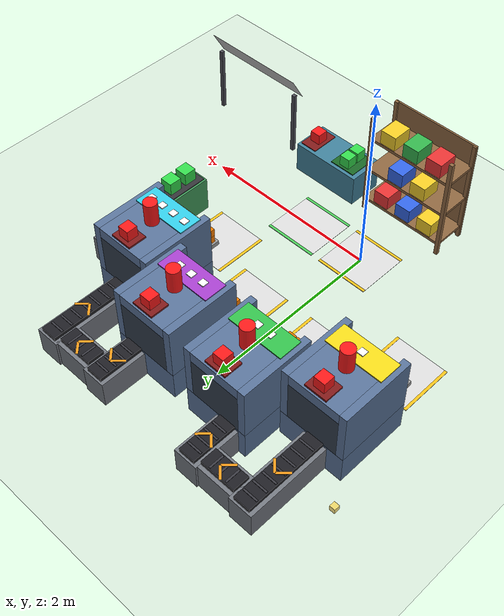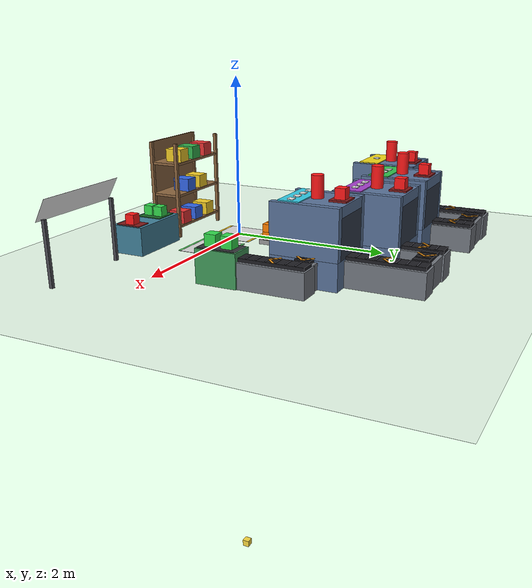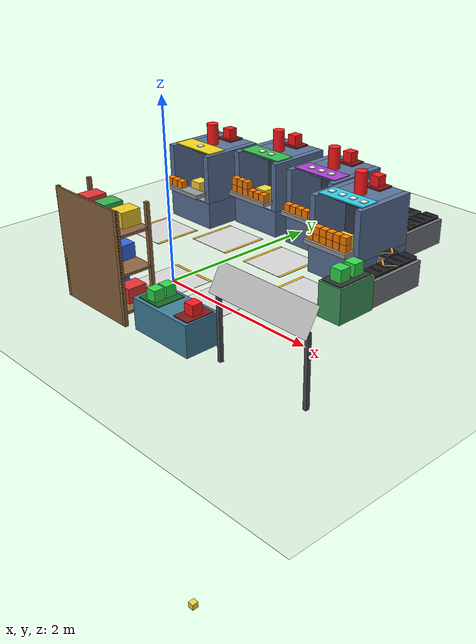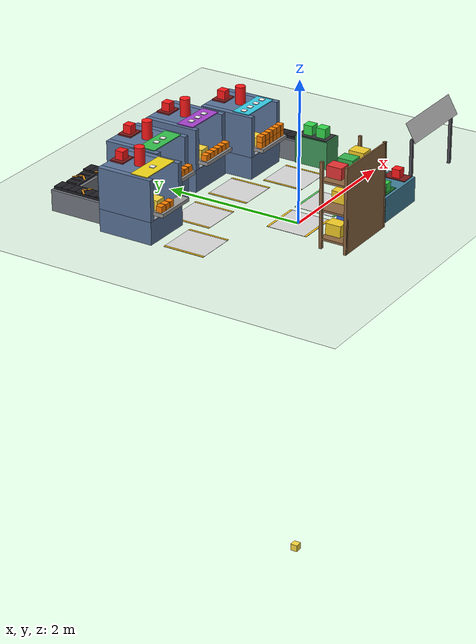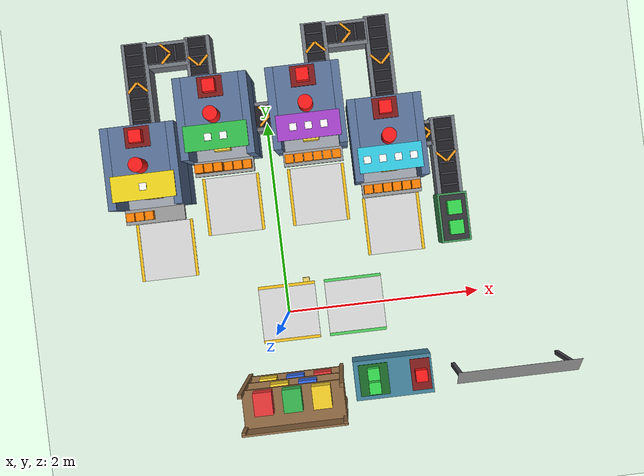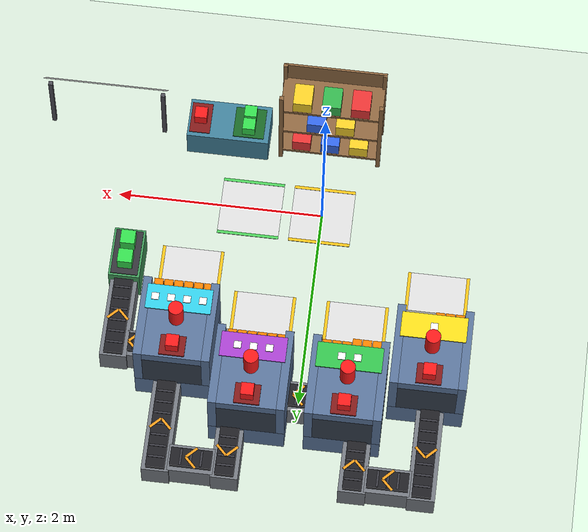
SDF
<?xml version="1.0"?>
<!-- Task B1 world (generated file; the generator is not part of this repository) -->
<sdf version="1.6">
  <world name="factory">
    <include><uri>model://sun</uri></include>
    <include><uri>model://ground_plane</uri></include>
    <scene><ambient>0.55 0.55 0.55 1</ambient><shadows>false</shadows></scene>
    <physics type="ode">
      <max_step_size>0.001</max_step_size>
      <real_time_factor>1</real_time_factor>
      <real_time_update_rate>1000</real_time_update_rate>
    </physics>
    <!-- 真値の取得用（/model_states, /get_entity_state, /set_entity_state） -->
    <plugin name="gazebo_ros_state" filename="libgazebo_ros_state.so">
      <ros><namespace>/</namespace></ros>
      <update_rate>50</update_rate>
    </plugin>
    <gui><camera name="user_camera"><pose>0.2 0.2 9.0 0 1.5 1.5708</pose></camera></gui>
    <plugin name="m5_visual" filename="libm5_visual_state.so"><period>1.0</period><work_ids>M1 M2 M3 M4</work_ids><stock_caps>M1:3 M2:9 M3:6 M4:12 FIN:2 NG1:1 NG2:1 NG3:1 NG4:1 DOCKS:2 DOCKX:1</stock_caps><flow_pieces>8</flow_pieces><flow_z>0.3920</flow_z></plugin>

    <model name="store">
      <static>true</static>
      <pose>0.0 0.0 0 0 0 3.141593</pose>
      <link name="base">
        <visual name="pad"><pose>0 0 0.002 0 0 0</pose><geometry><box><size>0.6 0.6 0.004</size></box></geometry><material><ambient>0.85 0.85 0.85 1</ambient><diffuse>0.85 0.85 0.85 1</diffuse><specular>0.1 0.1 0.1 1</specular></material></visual><visual name="pad_edge_l"><pose>0 0.285 0.003 0 0 0</pose><geometry><box><size>0.6 0.03 0.006</size></box></geometry><material><ambient>0.95 0.75 0.1 1</ambient><diffuse>0.95 0.75 0.1 1</diffuse><specular>0.1 0.1 0.1 1</specular></material></visual><visual name="pad_edge_r"><pose>0 -0.285 0.003 0 0 0</pose><geometry><box><size>0.6 0.03 0.006</size></box></geometry><material><ambient>0.95 0.75 0.1 1</ambient><diffuse>0.95 0.75 0.1 1</diffuse><specular>0.1 0.1 0.1 1</specular></material></visual>
        <visual name="post0"><pose>-0.48 0.62 0.6 0 0 0</pose><geometry><box><size>0.04 0.04 1.2</size></box></geometry><material><ambient>0.55 0.4 0.25 1</ambient><diffuse>0.55 0.4 0.25 1</diffuse><specular>0.1 0.1 0.1 1</specular></material></visual><collision name="post0"><pose>-0.48 0.62 0.6 0 0 0</pose><geometry><box><size>0.04 0.04 1.2</size></box></geometry></collision><visual name="post1"><pose>0.48 0.62 0.6 0 0 0</pose><geometry><box><size>0.04 0.04 1.2</size></box></geometry><material><ambient>0.55 0.4 0.25 1</ambient><diffuse>0.55 0.4 0.25 1</diffuse><specular>0.1 0.1 0.1 1</specular></material></visual><collision name="post1"><pose>0.48 0.62 0.6 0 0 0</pose><geometry><box><size>0.04 0.04 1.2</size></box></geometry></collision><visual name="post2"><pose>-0.48 0.9800000000000001 0.6 0 0 0</pose><geometry><box><size>0.04 0.04 1.2</size></box></geometry><material><ambient>0.55 0.4 0.25 1</ambient><diffuse>0.55 0.4 0.25 1</diffuse><specular>0.1 0.1 0.1 1</specular></material></visual><collision name="post2"><pose>-0.48 0.9800000000000001 0.6 0 0 0</pose><geometry><box><size>0.04 0.04 1.2</size></box></geometry></collision><visual name="post3"><pose>0.48 0.9800000000000001 0.6 0 0 0</pose><geometry><box><size>0.04 0.04 1.2</size></box></geometry><material><ambient>0.55 0.4 0.25 1</ambient><diffuse>0.55 0.4 0.25 1</diffuse><specular>0.1 0.1 0.1 1</specular></material></visual><collision name="post3"><pose>0.48 0.9800000000000001 0.6 0 0 0</pose><geometry><box><size>0.04 0.04 1.2</size></box></geometry></collision><visual name="back"><pose>0 0.99 0.6 0 0 0</pose><geometry><box><size>1.0 0.02 1.2</size></box></geometry><material><ambient>0.55 0.4 0.25 1</ambient><diffuse>0.55 0.4 0.25 1</diffuse><specular>0.1 0.1 0.1 1</specular></material></visual><collision name="back"><pose>0 0.99 0.6 0 0 0</pose><geometry><box><size>1.0 0.02 1.2</size></box></geometry></collision><visual name="board0"><pose>0 0.8 0.135 0 0 0</pose><geometry><box><size>0.98 0.38 0.03</size></box></geometry><material><ambient>0.55 0.4 0.25 1</ambient><diffuse>0.55 0.4 0.25 1</diffuse><specular>0.1 0.1 0.1 1</specular></material></visual><collision name="board0"><pose>0 0.8 0.135 0 0 0</pose><geometry><box><size>0.98 0.38 0.03</size></box></geometry></collision><visual name="board1"><pose>0 0.8 0.535 0 0 0</pose><geometry><box><size>0.98 0.38 0.03</size></box></geometry><material><ambient>0.55 0.4 0.25 1</ambient><diffuse>0.55 0.4 0.25 1</diffuse><specular>0.1 0.1 0.1 1</specular></material></visual><collision name="board1"><pose>0 0.8 0.535 0 0 0</pose><geometry><box><size>0.98 0.38 0.03</size></box></geometry></collision><visual name="board2"><pose>0 0.8 0.9349999999999999 0 0 0</pose><geometry><box><size>0.98 0.38 0.03</size></box></geometry><material><ambient>0.55 0.4 0.25 1</ambient><diffuse>0.55 0.4 0.25 1</diffuse><specular>0.1 0.1 0.1 1</specular></material></visual><collision name="board2"><pose>0 0.8 0.9349999999999999 0 0 0</pose><geometry><box><size>0.98 0.38 0.03</size></box></geometry></collision><visual name="crate0_0"><pose>-0.28 0.73 0.22999999999999998 0 0 0</pose><geometry><box><size>0.18 0.22 0.16</size></box></geometry><material><ambient>0.9 0.2 0.2 1</ambient><diffuse>0.9 0.2 0.2 1</diffuse><specular>0.1 0.1 0.1 1</specular></material></visual><collision name="crate0_0"><pose>-0.28 0.73 0.22999999999999998 0 0 0</pose><geometry><box><size>0.18 0.22 0.16</size></box></geometry></collision><visual name="crate0_1"><pose>0.0 0.73 0.22999999999999998 0 0 0</pose><geometry><box><size>0.18 0.22 0.16</size></box></geometry><material><ambient>0.2 0.4 0.9 1</ambient><diffuse>0.2 0.4 0.9 1</diffuse><specular>0.1 0.1 0.1 1</specular></material></visual><collision name="crate0_1"><pose>0.0 0.73 0.22999999999999998 0 0 0</pose><geometry><box><size>0.18 0.22 0.16</size></box></geometry></collision><visual name="crate0_2"><pose>0.28 0.73 0.22999999999999998 0 0 0</pose><geometry><box><size>0.18 0.22 0.16</size></box></geometry><material><ambient>0.95 0.8 0.15 1</ambient><diffuse>0.95 0.8 0.15 1</diffuse><specular>0.1 0.1 0.1 1</specular></material></visual><collision name="crate0_2"><pose>0.28 0.73 0.22999999999999998 0 0 0</pose><geometry><box><size>0.18 0.22 0.16</size></box></geometry></collision><visual name="crate1_0"><pose>-0.14 0.73 0.63 0 0 0</pose><geometry><box><size>0.18 0.22 0.16</size></box></geometry><material><ambient>0.2 0.4 0.9 1</ambient><diffuse>0.2 0.4 0.9 1</diffuse><specular>0.1 0.1 0.1 1</specular></material></visual><collision name="crate1_0"><pose>-0.14 0.73 0.63 0 0 0</pose><geometry><box><size>0.18 0.22 0.16</size></box></geometry></collision><visual name="crate1_1"><pose>0.14 0.73 0.63 0 0 0</pose><geometry><box><size>0.18 0.22 0.16</size></box></geometry><material><ambient>0.95 0.8 0.15 1</ambient><diffuse>0.95 0.8 0.15 1</diffuse><specular>0.1 0.1 0.1 1</specular></material></visual><collision name="crate1_1"><pose>0.14 0.73 0.63 0 0 0</pose><geometry><box><size>0.18 0.22 0.16</size></box></geometry></collision><visual name="crate2_0"><pose>-0.28 0.73 1.03 0 0 0</pose><geometry><box><size>0.18 0.22 0.16</size></box></geometry><material><ambient>0.95 0.8 0.15 1</ambient><diffuse>0.95 0.8 0.15 1</diffuse><specular>0.1 0.1 0.1 1</specular></material></visual><collision name="crate2_0"><pose>-0.28 0.73 1.03 0 0 0</pose><geometry><box><size>0.18 0.22 0.16</size></box></geometry></collision><visual name="crate2_1"><pose>0.0 0.73 1.03 0 0 0</pose><geometry><box><size>0.18 0.22 0.16</size></box></geometry><material><ambient>0.2 0.7 0.3 1</ambient><diffuse>0.2 0.7 0.3 1</diffuse><specular>0.1 0.1 0.1 1</specular></material></visual><collision name="crate2_1"><pose>0.0 0.73 1.03 0 0 0</pose><geometry><box><size>0.18 0.22 0.16</size></box></geometry></collision><visual name="crate2_2"><pose>0.28 0.73 1.03 0 0 0</pose><geometry><box><size>0.18 0.22 0.16</size></box></geometry><material><ambient>0.9 0.2 0.2 1</ambient><diffuse>0.9 0.2 0.2 1</diffuse><specular>0.1 0.1 0.1 1</specular></material></visual><collision name="crate2_2"><pose>0.28 0.73 1.03 0 0 0</pose><geometry><box><size>0.18 0.22 0.16</size></box></geometry></collision>
      </link>
    </model>
    <model name="M1">
      <static>true</static>
      <pose>-1.2 0.8 0 0 0 1.570796</pose>
      <link name="base">
        <visual name="pad"><pose>0 0 0.002 0 0 0</pose><geometry><box><size>0.6 0.6 0.004</size></box></geometry><material><ambient>0.85 0.85 0.85 1</ambient><diffuse>0.85 0.85 0.85 1</diffuse><specular>0.1 0.1 0.1 1</specular></material></visual><visual name="pad_edge_l"><pose>0 0.285 0.003 0 0 0</pose><geometry><box><size>0.6 0.03 0.006</size></box></geometry><material><ambient>0.95 0.75 0.1 1</ambient><diffuse>0.95 0.75 0.1 1</diffuse><specular>0.1 0.1 0.1 1</specular></material></visual><visual name="pad_edge_r"><pose>0 -0.285 0.003 0 0 0</pose><geometry><box><size>0.6 0.03 0.006</size></box></geometry><material><ambient>0.95 0.75 0.1 1</ambient><diffuse>0.95 0.75 0.1 1</diffuse><specular>0.1 0.1 0.1 1</specular></material></visual>
        <visual name="body_floor"><pose>0.85 0 0.16 0 0 0</pose><geometry><box><size>0.8 0.72 0.32</size></box></geometry><material><ambient>0.35 0.45 0.6 1</ambient><diffuse>0.35 0.45 0.6 1</diffuse><specular>0.1 0.1 0.1 1</specular></material></visual><visual name="body_wall_l"><pose>0.85 0.32 0.61 0 0 0</pose><geometry><box><size>0.8 0.07999999999999996 0.5800000000000001</size></box></geometry><material><ambient>0.35 0.45 0.6 1</ambient><diffuse>0.35 0.45 0.6 1</diffuse><specular>0.1 0.1 0.1 1</specular></material></visual><visual name="body_wall_r"><pose>0.85 -0.32 0.61 0 0 0</pose><geometry><box><size>0.8 0.07999999999999996 0.5800000000000001</size></box></geometry><material><ambient>0.35 0.45 0.6 1</ambient><diffuse>0.35 0.45 0.6 1</diffuse><specular>0.1 0.1 0.1 1</specular></material></visual><visual name="body_roof"><pose>1.0 0 0.8400000000000001 0 0 0</pose><geometry><box><size>0.5 0.56 0.12</size></box></geometry><material><ambient>0.35 0.45 0.6 1</ambient><diffuse>0.35 0.45 0.6 1</diffuse><specular>0.1 0.1 0.1 1</specular></material></visual><visual name="body_back"><pose>1.1 0 0.55 0 0 0</pose><geometry><box><size>0.30000000000000004 0.56 0.46</size></box></geometry><material><ambient>0.2 0.24 0.3 1</ambient><diffuse>0.2 0.24 0.3 1</diffuse><specular>0.1 0.1 0.1 1</specular></material></visual><visual name="bench"><pose>0.7 0 0.325 0 0 0</pose><geometry><box><size>0.5 0.56 0.01</size></box></geometry><material><ambient>0.62 0.64 0.68 1</ambient><diffuse>0.62 0.64 0.68 1</diffuse><specular>0.1 0.1 0.1 1</specular></material></visual>
        <collision name="body"><pose>0.85 0 0.45 0 0 0</pose><geometry><box><size>0.8 0.72 0.9</size></box></geometry></collision>
        <visual name="id_band"><pose>0.6499999999999999 0 0.906 0 0 0</pose><geometry><box><size>0.25 0.62 0.012</size></box></geometry><material><ambient>0.95 0.85 0.1 1</ambient><diffuse>0.95 0.85 0.1 1</diffuse><specular>0.1 0.1 0.1 1</specular></material></visual><visual name="id_dot1"><pose>0.6499999999999999 0.0 0.916 0 0 0</pose><geometry><box><size>0.07 0.07 0.012</size></box></geometry><material><ambient>1 1 1 1</ambient><diffuse>1 1 1 1</diffuse><specular>0.1 0.1 0.1 1</specular></material></visual>
        <visual name="tray"><pose>0.37499999999999994 0 0.425 0 0 0</pose><geometry><box><size>0.15 0.6 0.05</size></box></geometry><material><ambient>0.6 0.6 0.6 1</ambient><diffuse>0.6 0.6 0.6 1</diffuse><specular>0.1 0.1 0.1 1</specular></material></visual>
        <collision name="tray"><pose>0.37499999999999994 0 0.425 0 0 0</pose><geometry><box><size>0.15 0.6 0.05</size></box></geometry></collision>
      </link>
      <link name="lamp">
        <pose>0.85 0 1.025 0 0 0</pose>
        <visual name="lamp"><geometry><cylinder><radius>0.07</radius><length>0.25</length></cylinder></geometry><material><ambient>1 0.1 0.1 1</ambient><diffuse>1 0.1 0.1 1</diffuse><specular>0.1 0.1 0.1 1</specular><emissive>1 0.1 0.1 1</emissive></material></visual>
      </link>
      <link name="work">
        <pose>0.62 0 0.41000000000000003 0 0 0</pose>
        <visual name="work"><pose>0 0 0 0 0 0</pose><geometry><box><size>0.16 0.16 0.16</size></box></geometry><material><ambient>0.98 0.85 0.25 1</ambient><diffuse>0.98 0.85 0.25 1</diffuse><specular>0.1 0.1 0.1 1</specular></material></visual>
      </link>
      <link name="stock">
        <visual name="s0"><pose>0.37499999999999994 0.2375 0.4925 0 0 0</pose><geometry><box><size>0.085 0.085 0.085</size></box></geometry><material><ambient>1 0.5 0 1</ambient><diffuse>1 0.5 0 1</diffuse><specular>0.1 0.1 0.1 1</specular></material></visual><visual name="s1"><pose>0.37499999999999994 0.14250000000000002 0.4925 0 0 0</pose><geometry><box><size>0.085 0.085 0.085</size></box></geometry><material><ambient>1 0.5 0 1</ambient><diffuse>1 0.5 0 1</diffuse><specular>0.1 0.1 0.1 1</specular></material></visual><visual name="s2"><pose>0.37499999999999994 0.0475 0.4925 0 0 0</pose><geometry><box><size>0.085 0.085 0.085</size></box></geometry><material><ambient>1 0.5 0 1</ambient><diffuse>1 0.5 0 1</diffuse><specular>0.1 0.1 0.1 1</specular></material></visual>
      </link>
    </model>
    <model name="M2">
      <static>true</static>
      <pose>-0.45 1.2 0 0 0 1.570796</pose>
      <link name="base">
        <visual name="pad"><pose>0 0 0.002 0 0 0</pose><geometry><box><size>0.6 0.6 0.004</size></box></geometry><material><ambient>0.85 0.85 0.85 1</ambient><diffuse>0.85 0.85 0.85 1</diffuse><specular>0.1 0.1 0.1 1</specular></material></visual><visual name="pad_edge_l"><pose>0 0.285 0.003 0 0 0</pose><geometry><box><size>0.6 0.03 0.006</size></box></geometry><material><ambient>0.95 0.75 0.1 1</ambient><diffuse>0.95 0.75 0.1 1</diffuse><specular>0.1 0.1 0.1 1</specular></material></visual><visual name="pad_edge_r"><pose>0 -0.285 0.003 0 0 0</pose><geometry><box><size>0.6 0.03 0.006</size></box></geometry><material><ambient>0.95 0.75 0.1 1</ambient><diffuse>0.95 0.75 0.1 1</diffuse><specular>0.1 0.1 0.1 1</specular></material></visual>
        <visual name="body_floor"><pose>0.85 0 0.16 0 0 0</pose><geometry><box><size>0.8 0.72 0.32</size></box></geometry><material><ambient>0.35 0.45 0.6 1</ambient><diffuse>0.35 0.45 0.6 1</diffuse><specular>0.1 0.1 0.1 1</specular></material></visual><visual name="body_wall_l"><pose>0.85 0.32 0.61 0 0 0</pose><geometry><box><size>0.8 0.07999999999999996 0.5800000000000001</size></box></geometry><material><ambient>0.35 0.45 0.6 1</ambient><diffuse>0.35 0.45 0.6 1</diffuse><specular>0.1 0.1 0.1 1</specular></material></visual><visual name="body_wall_r"><pose>0.85 -0.32 0.61 0 0 0</pose><geometry><box><size>0.8 0.07999999999999996 0.5800000000000001</size></box></geometry><material><ambient>0.35 0.45 0.6 1</ambient><diffuse>0.35 0.45 0.6 1</diffuse><specular>0.1 0.1 0.1 1</specular></material></visual><visual name="body_roof"><pose>1.0 0 0.8400000000000001 0 0 0</pose><geometry><box><size>0.5 0.56 0.12</size></box></geometry><material><ambient>0.35 0.45 0.6 1</ambient><diffuse>0.35 0.45 0.6 1</diffuse><specular>0.1 0.1 0.1 1</specular></material></visual><visual name="body_back"><pose>1.1 0 0.55 0 0 0</pose><geometry><box><size>0.30000000000000004 0.56 0.46</size></box></geometry><material><ambient>0.2 0.24 0.3 1</ambient><diffuse>0.2 0.24 0.3 1</diffuse><specular>0.1 0.1 0.1 1</specular></material></visual><visual name="bench"><pose>0.7 0 0.325 0 0 0</pose><geometry><box><size>0.5 0.56 0.01</size></box></geometry><material><ambient>0.62 0.64 0.68 1</ambient><diffuse>0.62 0.64 0.68 1</diffuse><specular>0.1 0.1 0.1 1</specular></material></visual>
        <collision name="body"><pose>0.85 0 0.45 0 0 0</pose><geometry><box><size>0.8 0.72 0.9</size></box></geometry></collision>
        <visual name="id_band"><pose>0.6499999999999999 0 0.906 0 0 0</pose><geometry><box><size>0.25 0.62 0.012</size></box></geometry><material><ambient>0.2 0.75 0.3 1</ambient><diffuse>0.2 0.75 0.3 1</diffuse><specular>0.1 0.1 0.1 1</specular></material></visual><visual name="id_dot1"><pose>0.6499999999999999 -0.075 0.916 0 0 0</pose><geometry><box><size>0.07 0.07 0.012</size></box></geometry><material><ambient>1 1 1 1</ambient><diffuse>1 1 1 1</diffuse><specular>0.1 0.1 0.1 1</specular></material></visual><visual name="id_dot2"><pose>0.6499999999999999 0.075 0.916 0 0 0</pose><geometry><box><size>0.07 0.07 0.012</size></box></geometry><material><ambient>1 1 1 1</ambient><diffuse>1 1 1 1</diffuse><specular>0.1 0.1 0.1 1</specular></material></visual>
        <visual name="tray"><pose>0.37499999999999994 0 0.425 0 0 0</pose><geometry><box><size>0.15 0.6 0.05</size></box></geometry><material><ambient>0.6 0.6 0.6 1</ambient><diffuse>0.6 0.6 0.6 1</diffuse><specular>0.1 0.1 0.1 1</specular></material></visual>
        <collision name="tray"><pose>0.37499999999999994 0 0.425 0 0 0</pose><geometry><box><size>0.15 0.6 0.05</size></box></geometry></collision>
      </link>
      <link name="lamp">
        <pose>0.85 0 1.025 0 0 0</pose>
        <visual name="lamp"><geometry><cylinder><radius>0.07</radius><length>0.25</length></cylinder></geometry><material><ambient>1 0.1 0.1 1</ambient><diffuse>1 0.1 0.1 1</diffuse><specular>0.1 0.1 0.1 1</specular><emissive>1 0.1 0.1 1</emissive></material></visual>
      </link>
      <link name="work">
        <pose>0.62 0 0.41000000000000003 0 0 0</pose>
        <visual name="work"><pose>0 0 0 0 0 0</pose><geometry><box><size>0.16 0.16 0.16</size></box></geometry><material><ambient>0.98 0.85 0.25 1</ambient><diffuse>0.98 0.85 0.25 1</diffuse><specular>0.1 0.1 0.1 1</specular></material></visual>
      </link>
      <link name="stock">
        <visual name="s0"><pose>0.37499999999999994 0.2375 0.4925 0 0 0</pose><geometry><box><size>0.085 0.085 0.085</size></box></geometry><material><ambient>1 0.5 0 1</ambient><diffuse>1 0.5 0 1</diffuse><specular>0.1 0.1 0.1 1</specular></material></visual><visual name="s1"><pose>0.37499999999999994 0.14250000000000002 0.4925 0 0 0</pose><geometry><box><size>0.085 0.085 0.085</size></box></geometry><material><ambient>1 0.5 0 1</ambient><diffuse>1 0.5 0 1</diffuse><specular>0.1 0.1 0.1 1</specular></material></visual><visual name="s2"><pose>0.37499999999999994 0.0475 0.4925 0 0 0</pose><geometry><box><size>0.085 0.085 0.085</size></box></geometry><material><ambient>1 0.5 0 1</ambient><diffuse>1 0.5 0 1</diffuse><specular>0.1 0.1 0.1 1</specular></material></visual><visual name="s3"><pose>0.37499999999999994 -0.0475 0.4925 0 0 0</pose><geometry><box><size>0.085 0.085 0.085</size></box></geometry><material><ambient>1 0.5 0 1</ambient><diffuse>1 0.5 0 1</diffuse><specular>0.1 0.1 0.1 1</specular></material></visual><visual name="s4"><pose>0.37499999999999994 -0.14250000000000002 0.4925 0 0 0</pose><geometry><box><size>0.085 0.085 0.085</size></box></geometry><material><ambient>1 0.5 0 1</ambient><diffuse>1 0.5 0 1</diffuse><specular>0.1 0.1 0.1 1</specular></material></visual><visual name="s5"><pose>0.37499999999999994 -0.2375 0.4925 0 0 0</pose><geometry><box><size>0.085 0.085 0.085</size></box></geometry><material><ambient>1 0.5 0 1</ambient><diffuse>1 0.5 0 1</diffuse><specular>0.1 0.1 0.1 1</specular></material></visual><visual name="s6"><pose>0.37499999999999994 0.2375 0.5775 0 0 0</pose><geometry><box><size>0.085 0.085 0.085</size></box></geometry><material><ambient>1 0.5 0 1</ambient><diffuse>1 0.5 0 1</diffuse><specular>0.1 0.1 0.1 1</specular></material></visual><visual name="s7"><pose>0.37499999999999994 0.14250000000000002 0.5775 0 0 0</pose><geometry><box><size>0.085 0.085 0.085</size></box></geometry><material><ambient>1 0.5 0 1</ambient><diffuse>1 0.5 0 1</diffuse><specular>0.1 0.1 0.1 1</specular></material></visual><visual name="s8"><pose>0.37499999999999994 0.0475 0.5775 0 0 0</pose><geometry><box><size>0.085 0.085 0.085</size></box></geometry><material><ambient>1 0.5 0 1</ambient><diffuse>1 0.5 0 1</diffuse><specular>0.1 0.1 0.1 1</specular></material></visual>
      </link>
    </model>
    <model name="M3">
      <static>true</static>
      <pose>0.45 1.2 0 0 0 1.570796</pose>
      <link name="base">
        <visual name="pad"><pose>0 0 0.002 0 0 0</pose><geometry><box><size>0.6 0.6 0.004</size></box></geometry><material><ambient>0.85 0.85 0.85 1</ambient><diffuse>0.85 0.85 0.85 1</diffuse><specular>0.1 0.1 0.1 1</specular></material></visual><visual name="pad_edge_l"><pose>0 0.285 0.003 0 0 0</pose><geometry><box><size>0.6 0.03 0.006</size></box></geometry><material><ambient>0.95 0.75 0.1 1</ambient><diffuse>0.95 0.75 0.1 1</diffuse><specular>0.1 0.1 0.1 1</specular></material></visual><visual name="pad_edge_r"><pose>0 -0.285 0.003 0 0 0</pose><geometry><box><size>0.6 0.03 0.006</size></box></geometry><material><ambient>0.95 0.75 0.1 1</ambient><diffuse>0.95 0.75 0.1 1</diffuse><specular>0.1 0.1 0.1 1</specular></material></visual>
        <visual name="body_floor"><pose>0.85 0 0.16 0 0 0</pose><geometry><box><size>0.8 0.72 0.32</size></box></geometry><material><ambient>0.35 0.45 0.6 1</ambient><diffuse>0.35 0.45 0.6 1</diffuse><specular>0.1 0.1 0.1 1</specular></material></visual><visual name="body_wall_l"><pose>0.85 0.32 0.61 0 0 0</pose><geometry><box><size>0.8 0.07999999999999996 0.5800000000000001</size></box></geometry><material><ambient>0.35 0.45 0.6 1</ambient><diffuse>0.35 0.45 0.6 1</diffuse><specular>0.1 0.1 0.1 1</specular></material></visual><visual name="body_wall_r"><pose>0.85 -0.32 0.61 0 0 0</pose><geometry><box><size>0.8 0.07999999999999996 0.5800000000000001</size></box></geometry><material><ambient>0.35 0.45 0.6 1</ambient><diffuse>0.35 0.45 0.6 1</diffuse><specular>0.1 0.1 0.1 1</specular></material></visual><visual name="body_roof"><pose>1.0 0 0.8400000000000001 0 0 0</pose><geometry><box><size>0.5 0.56 0.12</size></box></geometry><material><ambient>0.35 0.45 0.6 1</ambient><diffuse>0.35 0.45 0.6 1</diffuse><specular>0.1 0.1 0.1 1</specular></material></visual><visual name="body_back"><pose>1.1 0 0.55 0 0 0</pose><geometry><box><size>0.30000000000000004 0.56 0.46</size></box></geometry><material><ambient>0.2 0.24 0.3 1</ambient><diffuse>0.2 0.24 0.3 1</diffuse><specular>0.1 0.1 0.1 1</specular></material></visual><visual name="bench"><pose>0.7 0 0.325 0 0 0</pose><geometry><box><size>0.5 0.56 0.01</size></box></geometry><material><ambient>0.62 0.64 0.68 1</ambient><diffuse>0.62 0.64 0.68 1</diffuse><specular>0.1 0.1 0.1 1</specular></material></visual>
        <collision name="body"><pose>0.85 0 0.45 0 0 0</pose><geometry><box><size>0.8 0.72 0.9</size></box></geometry></collision>
        <visual name="id_band"><pose>0.6499999999999999 0 0.906 0 0 0</pose><geometry><box><size>0.25 0.62 0.012</size></box></geometry><material><ambient>0.65 0.25 0.8 1</ambient><diffuse>0.65 0.25 0.8 1</diffuse><specular>0.1 0.1 0.1 1</specular></material></visual><visual name="id_dot1"><pose>0.6499999999999999 -0.15 0.916 0 0 0</pose><geometry><box><size>0.07 0.07 0.012</size></box></geometry><material><ambient>1 1 1 1</ambient><diffuse>1 1 1 1</diffuse><specular>0.1 0.1 0.1 1</specular></material></visual><visual name="id_dot2"><pose>0.6499999999999999 0.0 0.916 0 0 0</pose><geometry><box><size>0.07 0.07 0.012</size></box></geometry><material><ambient>1 1 1 1</ambient><diffuse>1 1 1 1</diffuse><specular>0.1 0.1 0.1 1</specular></material></visual><visual name="id_dot3"><pose>0.6499999999999999 0.15 0.916 0 0 0</pose><geometry><box><size>0.07 0.07 0.012</size></box></geometry><material><ambient>1 1 1 1</ambient><diffuse>1 1 1 1</diffuse><specular>0.1 0.1 0.1 1</specular></material></visual>
        <visual name="tray"><pose>0.37499999999999994 0 0.425 0 0 0</pose><geometry><box><size>0.15 0.6 0.05</size></box></geometry><material><ambient>0.6 0.6 0.6 1</ambient><diffuse>0.6 0.6 0.6 1</diffuse><specular>0.1 0.1 0.1 1</specular></material></visual>
        <collision name="tray"><pose>0.37499999999999994 0 0.425 0 0 0</pose><geometry><box><size>0.15 0.6 0.05</size></box></geometry></collision>
      </link>
      <link name="lamp">
        <pose>0.85 0 1.025 0 0 0</pose>
        <visual name="lamp"><geometry><cylinder><radius>0.07</radius><length>0.25</length></cylinder></geometry><material><ambient>1 0.1 0.1 1</ambient><diffuse>1 0.1 0.1 1</diffuse><specular>0.1 0.1 0.1 1</specular><emissive>1 0.1 0.1 1</emissive></material></visual>
      </link>
      <link name="work">
        <pose>0.62 0 0.41000000000000003 0 0 0</pose>
        <visual name="work"><pose>0 0 0 0 0 0</pose><geometry><box><size>0.16 0.16 0.16</size></box></geometry><material><ambient>0.98 0.85 0.25 1</ambient><diffuse>0.98 0.85 0.25 1</diffuse><specular>0.1 0.1 0.1 1</specular></material></visual>
      </link>
      <link name="stock">
        <visual name="s0"><pose>0.37499999999999994 0.2375 0.4925 0 0 0</pose><geometry><box><size>0.085 0.085 0.085</size></box></geometry><material><ambient>1 0.5 0 1</ambient><diffuse>1 0.5 0 1</diffuse><specular>0.1 0.1 0.1 1</specular></material></visual><visual name="s1"><pose>0.37499999999999994 0.14250000000000002 0.4925 0 0 0</pose><geometry><box><size>0.085 0.085 0.085</size></box></geometry><material><ambient>1 0.5 0 1</ambient><diffuse>1 0.5 0 1</diffuse><specular>0.1 0.1 0.1 1</specular></material></visual><visual name="s2"><pose>0.37499999999999994 0.0475 0.4925 0 0 0</pose><geometry><box><size>0.085 0.085 0.085</size></box></geometry><material><ambient>1 0.5 0 1</ambient><diffuse>1 0.5 0 1</diffuse><specular>0.1 0.1 0.1 1</specular></material></visual><visual name="s3"><pose>0.37499999999999994 -0.0475 0.4925 0 0 0</pose><geometry><box><size>0.085 0.085 0.085</size></box></geometry><material><ambient>1 0.5 0 1</ambient><diffuse>1 0.5 0 1</diffuse><specular>0.1 0.1 0.1 1</specular></material></visual><visual name="s4"><pose>0.37499999999999994 -0.14250000000000002 0.4925 0 0 0</pose><geometry><box><size>0.085 0.085 0.085</size></box></geometry><material><ambient>1 0.5 0 1</ambient><diffuse>1 0.5 0 1</diffuse><specular>0.1 0.1 0.1 1</specular></material></visual><visual name="s5"><pose>0.37499999999999994 -0.2375 0.4925 0 0 0</pose><geometry><box><size>0.085 0.085 0.085</size></box></geometry><material><ambient>1 0.5 0 1</ambient><diffuse>1 0.5 0 1</diffuse><specular>0.1 0.1 0.1 1</specular></material></visual>
      </link>
    </model>
    <model name="M4">
      <static>true</static>
      <pose>1.2 0.8 0 0 0 1.570796</pose>
      <link name="base">
        <visual name="pad"><pose>0 0 0.002 0 0 0</pose><geometry><box><size>0.6 0.6 0.004</size></box></geometry><material><ambient>0.85 0.85 0.85 1</ambient><diffuse>0.85 0.85 0.85 1</diffuse><specular>0.1 0.1 0.1 1</specular></material></visual><visual name="pad_edge_l"><pose>0 0.285 0.003 0 0 0</pose><geometry><box><size>0.6 0.03 0.006</size></box></geometry><material><ambient>0.95 0.75 0.1 1</ambient><diffuse>0.95 0.75 0.1 1</diffuse><specular>0.1 0.1 0.1 1</specular></material></visual><visual name="pad_edge_r"><pose>0 -0.285 0.003 0 0 0</pose><geometry><box><size>0.6 0.03 0.006</size></box></geometry><material><ambient>0.95 0.75 0.1 1</ambient><diffuse>0.95 0.75 0.1 1</diffuse><specular>0.1 0.1 0.1 1</specular></material></visual>
        <visual name="body_floor"><pose>0.85 0 0.16 0 0 0</pose><geometry><box><size>0.8 0.72 0.32</size></box></geometry><material><ambient>0.35 0.45 0.6 1</ambient><diffuse>0.35 0.45 0.6 1</diffuse><specular>0.1 0.1 0.1 1</specular></material></visual><visual name="body_wall_l"><pose>0.85 0.32 0.61 0 0 0</pose><geometry><box><size>0.8 0.07999999999999996 0.5800000000000001</size></box></geometry><material><ambient>0.35 0.45 0.6 1</ambient><diffuse>0.35 0.45 0.6 1</diffuse><specular>0.1 0.1 0.1 1</specular></material></visual><visual name="body_wall_r"><pose>0.85 -0.32 0.61 0 0 0</pose><geometry><box><size>0.8 0.07999999999999996 0.5800000000000001</size></box></geometry><material><ambient>0.35 0.45 0.6 1</ambient><diffuse>0.35 0.45 0.6 1</diffuse><specular>0.1 0.1 0.1 1</specular></material></visual><visual name="body_roof"><pose>1.0 0 0.8400000000000001 0 0 0</pose><geometry><box><size>0.5 0.56 0.12</size></box></geometry><material><ambient>0.35 0.45 0.6 1</ambient><diffuse>0.35 0.45 0.6 1</diffuse><specular>0.1 0.1 0.1 1</specular></material></visual><visual name="body_back"><pose>1.1 0 0.55 0 0 0</pose><geometry><box><size>0.30000000000000004 0.56 0.46</size></box></geometry><material><ambient>0.2 0.24 0.3 1</ambient><diffuse>0.2 0.24 0.3 1</diffuse><specular>0.1 0.1 0.1 1</specular></material></visual><visual name="bench"><pose>0.7 0 0.325 0 0 0</pose><geometry><box><size>0.5 0.56 0.01</size></box></geometry><material><ambient>0.62 0.64 0.68 1</ambient><diffuse>0.62 0.64 0.68 1</diffuse><specular>0.1 0.1 0.1 1</specular></material></visual>
        <collision name="body"><pose>0.85 0 0.45 0 0 0</pose><geometry><box><size>0.8 0.72 0.9</size></box></geometry></collision>
        <visual name="id_band"><pose>0.6499999999999999 0 0.906 0 0 0</pose><geometry><box><size>0.25 0.62 0.012</size></box></geometry><material><ambient>0.2 0.8 0.9 1</ambient><diffuse>0.2 0.8 0.9 1</diffuse><specular>0.1 0.1 0.1 1</specular></material></visual><visual name="id_dot1"><pose>0.6499999999999999 -0.22499999999999998 0.916 0 0 0</pose><geometry><box><size>0.07 0.07 0.012</size></box></geometry><material><ambient>1 1 1 1</ambient><diffuse>1 1 1 1</diffuse><specular>0.1 0.1 0.1 1</specular></material></visual><visual name="id_dot2"><pose>0.6499999999999999 -0.075 0.916 0 0 0</pose><geometry><box><size>0.07 0.07 0.012</size></box></geometry><material><ambient>1 1 1 1</ambient><diffuse>1 1 1 1</diffuse><specular>0.1 0.1 0.1 1</specular></material></visual><visual name="id_dot3"><pose>0.6499999999999999 0.075 0.916 0 0 0</pose><geometry><box><size>0.07 0.07 0.012</size></box></geometry><material><ambient>1 1 1 1</ambient><diffuse>1 1 1 1</diffuse><specular>0.1 0.1 0.1 1</specular></material></visual><visual name="id_dot4"><pose>0.6499999999999999 0.22499999999999998 0.916 0 0 0</pose><geometry><box><size>0.07 0.07 0.012</size></box></geometry><material><ambient>1 1 1 1</ambient><diffuse>1 1 1 1</diffuse><specular>0.1 0.1 0.1 1</specular></material></visual>
        <visual name="tray"><pose>0.37499999999999994 0 0.425 0 0 0</pose><geometry><box><size>0.15 0.6 0.05</size></box></geometry><material><ambient>0.6 0.6 0.6 1</ambient><diffuse>0.6 0.6 0.6 1</diffuse><specular>0.1 0.1 0.1 1</specular></material></visual>
        <collision name="tray"><pose>0.37499999999999994 0 0.425 0 0 0</pose><geometry><box><size>0.15 0.6 0.05</size></box></geometry></collision>
      </link>
      <link name="lamp">
        <pose>0.85 0 1.025 0 0 0</pose>
        <visual name="lamp"><geometry><cylinder><radius>0.07</radius><length>0.25</length></cylinder></geometry><material><ambient>1 0.1 0.1 1</ambient><diffuse>1 0.1 0.1 1</diffuse><specular>0.1 0.1 0.1 1</specular><emissive>1 0.1 0.1 1</emissive></material></visual>
      </link>
      <link name="work">
        <pose>0.62 0 0.41000000000000003 0 0 0</pose>
        <visual name="work"><pose>0 0 0 0 0 0</pose><geometry><box><size>0.16 0.16 0.16</size></box></geometry><material><ambient>0.98 0.85 0.25 1</ambient><diffuse>0.98 0.85 0.25 1</diffuse><specular>0.1 0.1 0.1 1</specular></material></visual>
      </link>
      <link name="stock">
        <visual name="s0"><pose>0.37499999999999994 0.2375 0.4925 0 0 0</pose><geometry><box><size>0.085 0.085 0.085</size></box></geometry><material><ambient>1 0.5 0 1</ambient><diffuse>1 0.5 0 1</diffuse><specular>0.1 0.1 0.1 1</specular></material></visual><visual name="s1"><pose>0.37499999999999994 0.14250000000000002 0.4925 0 0 0</pose><geometry><box><size>0.085 0.085 0.085</size></box></geometry><material><ambient>1 0.5 0 1</ambient><diffuse>1 0.5 0 1</diffuse><specular>0.1 0.1 0.1 1</specular></material></visual><visual name="s2"><pose>0.37499999999999994 0.0475 0.4925 0 0 0</pose><geometry><box><size>0.085 0.085 0.085</size></box></geometry><material><ambient>1 0.5 0 1</ambient><diffuse>1 0.5 0 1</diffuse><specular>0.1 0.1 0.1 1</specular></material></visual><visual name="s3"><pose>0.37499999999999994 -0.0475 0.4925 0 0 0</pose><geometry><box><size>0.085 0.085 0.085</size></box></geometry><material><ambient>1 0.5 0 1</ambient><diffuse>1 0.5 0 1</diffuse><specular>0.1 0.1 0.1 1</specular></material></visual><visual name="s4"><pose>0.37499999999999994 -0.14250000000000002 0.4925 0 0 0</pose><geometry><box><size>0.085 0.085 0.085</size></box></geometry><material><ambient>1 0.5 0 1</ambient><diffuse>1 0.5 0 1</diffuse><specular>0.1 0.1 0.1 1</specular></material></visual><visual name="s5"><pose>0.37499999999999994 -0.2375 0.4925 0 0 0</pose><geometry><box><size>0.085 0.085 0.085</size></box></geometry><material><ambient>1 0.5 0 1</ambient><diffuse>1 0.5 0 1</diffuse><specular>0.1 0.1 0.1 1</specular></material></visual><visual name="s6"><pose>0.37499999999999994 0.2375 0.5775 0 0 0</pose><geometry><box><size>0.085 0.085 0.085</size></box></geometry><material><ambient>1 0.5 0 1</ambient><diffuse>1 0.5 0 1</diffuse><specular>0.1 0.1 0.1 1</specular></material></visual><visual name="s7"><pose>0.37499999999999994 0.14250000000000002 0.5775 0 0 0</pose><geometry><box><size>0.085 0.085 0.085</size></box></geometry><material><ambient>1 0.5 0 1</ambient><diffuse>1 0.5 0 1</diffuse><specular>0.1 0.1 0.1 1</specular></material></visual><visual name="s8"><pose>0.37499999999999994 0.0475 0.5775 0 0 0</pose><geometry><box><size>0.085 0.085 0.085</size></box></geometry><material><ambient>1 0.5 0 1</ambient><diffuse>1 0.5 0 1</diffuse><specular>0.1 0.1 0.1 1</specular></material></visual><visual name="s9"><pose>0.37499999999999994 -0.0475 0.5775 0 0 0</pose><geometry><box><size>0.085 0.085 0.085</size></box></geometry><material><ambient>1 0.5 0 1</ambient><diffuse>1 0.5 0 1</diffuse><specular>0.1 0.1 0.1 1</specular></material></visual><visual name="s10"><pose>0.37499999999999994 -0.14250000000000002 0.5775 0 0 0</pose><geometry><box><size>0.085 0.085 0.085</size></box></geometry><material><ambient>1 0.5 0 1</ambient><diffuse>1 0.5 0 1</diffuse><specular>0.1 0.1 0.1 1</specular></material></visual><visual name="s11"><pose>0.37499999999999994 -0.2375 0.5775 0 0 0</pose><geometry><box><size>0.085 0.085 0.085</size></box></geometry><material><ambient>1 0.5 0 1</ambient><diffuse>1 0.5 0 1</diffuse><specular>0.1 0.1 0.1 1</specular></material></visual>
      </link>
    </model>
    <model name="fin_table"><static>true</static><pose>1.7999999999999998 0.8 0 0 0 0</pose><link name="base">
      <visual name="table"><pose>0 0 0.2 0 0 0</pose><geometry><box><size>0.3 0.5 0.4</size></box></geometry><material><ambient>0.25 0.6 0.35 1</ambient><diffuse>0.25 0.6 0.35 1</diffuse><specular>0.1 0.1 0.1 1</specular></material></visual>
      <collision name="table"><pose>0 0 0.2 0 0 0</pose><geometry><box><size>0.3 0.5 0.4</size></box></geometry></collision>
      <visual name="rim"><pose>0 0 0.405 0 0 0</pose><geometry><box><size>0.26 0.46 0.01</size></box></geometry><material><ambient>0.2 0.2 0.22 1</ambient><diffuse>0.2 0.2 0.22 1</diffuse><specular>0.1 0.1 0.1 1</specular></material></visual>
    </link></model>
    <model name="FIN"><static>true</static><pose>1.7999999999999998 0.8 0 0 0 0</pose><link name="stock"><visual name="s0"><pose>0.0 0.1 0.48000000000000004 0 0 0</pose><geometry><box><size>0.14 0.14 0.14</size></box></geometry><material><ambient>0.2 0.85 0.3 1</ambient><diffuse>0.2 0.85 0.3 1</diffuse><specular>0.1 0.1 0.1 1</specular></material></visual><visual name="s1"><pose>0.0 -0.1 0.48000000000000004 0 0 0</pose><geometry><box><size>0.14 0.14 0.14</size></box></geometry><material><ambient>0.2 0.85 0.3 1</ambient><diffuse>0.2 0.85 0.3 1</diffuse><specular>0.1 0.1 0.1 1</specular></material></visual></link></model>
    <model name="conv_M1_M2_a">
      <static>true</static>
      <pose>-1.25 2.49 0 0 0 1.57080</pose>
      <link name="base">
        <visual name="table"><pose>0 0 0.15 0 0 0</pose><geometry><box><size>0.9200000000000004 0.26 0.3</size></box></geometry><material><ambient>0.45 0.47 0.5 1</ambient><diffuse>0.45 0.47 0.5 1</diffuse><specular>0.1 0.1 0.1 1</specular></material></visual><collision name="table"><pose>0 0 0.15 0 0 0</pose><geometry><box><size>0.9200000000000004 0.26 0.3</size></box></geometry></collision><visual name="belt"><pose>0 0 0.32 0 0 0</pose><geometry><box><size>0.8800000000000003 0.18 0.04</size></box></geometry><material><ambient>0.12 0.12 0.14 1</ambient><diffuse>0.12 0.12 0.14 1</diffuse><specular>0.1 0.1 0.1 1</specular></material></visual><visual name="belt_rib0"><pose>-0.33428571428571446 0 0.34199999999999997 0 0 0</pose><geometry><box><size>0.02 0.16 0.004</size></box></geometry><material><ambient>0.22 0.22 0.25 1</ambient><diffuse>0.22 0.22 0.25 1</diffuse><specular>0.1 0.1 0.1 1</specular></material></visual><visual name="belt_rib1"><pose>-0.22285714285714298 0 0.34199999999999997 0 0 0</pose><geometry><box><size>0.02 0.16 0.004</size></box></geometry><material><ambient>0.22 0.22 0.25 1</ambient><diffuse>0.22 0.22 0.25 1</diffuse><specular>0.1 0.1 0.1 1</specular></material></visual><visual name="belt_rib2"><pose>-0.11142857142857149 0 0.34199999999999997 0 0 0</pose><geometry><box><size>0.02 0.16 0.004</size></box></geometry><material><ambient>0.22 0.22 0.25 1</ambient><diffuse>0.22 0.22 0.25 1</diffuse><specular>0.1 0.1 0.1 1</specular></material></visual><visual name="belt_rib3"><pose>0.0 0 0.34199999999999997 0 0 0</pose><geometry><box><size>0.02 0.16 0.004</size></box></geometry><material><ambient>0.22 0.22 0.25 1</ambient><diffuse>0.22 0.22 0.25 1</diffuse><specular>0.1 0.1 0.1 1</specular></material></visual><visual name="belt_rib4"><pose>0.11142857142857149 0 0.34199999999999997 0 0 0</pose><geometry><box><size>0.02 0.16 0.004</size></box></geometry><material><ambient>0.22 0.22 0.25 1</ambient><diffuse>0.22 0.22 0.25 1</diffuse><specular>0.1 0.1 0.1 1</specular></material></visual><visual name="belt_rib5"><pose>0.22285714285714292 0 0.34199999999999997 0 0 0</pose><geometry><box><size>0.02 0.16 0.004</size></box></geometry><material><ambient>0.22 0.22 0.25 1</ambient><diffuse>0.22 0.22 0.25 1</diffuse><specular>0.1 0.1 0.1 1</specular></material></visual><visual name="belt_rib6"><pose>0.33428571428571446 0 0.34199999999999997 0 0 0</pose><geometry><box><size>0.02 0.16 0.004</size></box></geometry><material><ambient>0.22 0.22 0.25 1</ambient><diffuse>0.22 0.22 0.25 1</diffuse><specular>0.1 0.1 0.1 1</specular></material></visual><visual name="flow0_0"><pose>0.0 0.05 0.344 0 0 -0.78540</pose><geometry><box><size>0.14 0.025 0.006</size></box></geometry><material><ambient>0.95 0.6 0.1 1</ambient><diffuse>0.95 0.6 0.1 1</diffuse><specular>0.1 0.1 0.1 1</specular></material></visual><visual name="flow0_1"><pose>0.0 -0.05 0.344 0 0 0.78540</pose><geometry><box><size>0.14 0.025 0.006</size></box></geometry><material><ambient>0.95 0.6 0.1 1</ambient><diffuse>0.95 0.6 0.1 1</diffuse><specular>0.1 0.1 0.1 1</specular></material></visual>
      </link>
    </model>
    <model name="conv_M1_M2_b">
      <static>true</static>
      <pose>-0.925 2.8000000000000003 0 0 0 0</pose>
      <link name="base">
        <visual name="table"><pose>0 0 0.15 0 0 0</pose><geometry><box><size>0.4300000000000001 0.26 0.3</size></box></geometry><material><ambient>0.45 0.47 0.5 1</ambient><diffuse>0.45 0.47 0.5 1</diffuse><specular>0.1 0.1 0.1 1</specular></material></visual><collision name="table"><pose>0 0 0.15 0 0 0</pose><geometry><box><size>0.4300000000000001 0.26 0.3</size></box></geometry></collision><visual name="belt"><pose>0 0 0.32 0 0 0</pose><geometry><box><size>0.3900000000000001 0.18 0.04</size></box></geometry><material><ambient>0.12 0.12 0.14 1</ambient><diffuse>0.12 0.12 0.14 1</diffuse><specular>0.1 0.1 0.1 1</specular></material></visual><visual name="belt_rib0"><pose>-0.09666666666666672 0 0.34199999999999997 0 0 0</pose><geometry><box><size>0.02 0.16 0.004</size></box></geometry><material><ambient>0.22 0.22 0.25 1</ambient><diffuse>0.22 0.22 0.25 1</diffuse><specular>0.1 0.1 0.1 1</specular></material></visual><visual name="belt_rib1"><pose>0.0 0 0.34199999999999997 0 0 0</pose><geometry><box><size>0.02 0.16 0.004</size></box></geometry><material><ambient>0.22 0.22 0.25 1</ambient><diffuse>0.22 0.22 0.25 1</diffuse><specular>0.1 0.1 0.1 1</specular></material></visual><visual name="belt_rib2"><pose>0.09666666666666673 0 0.34199999999999997 0 0 0</pose><geometry><box><size>0.02 0.16 0.004</size></box></geometry><material><ambient>0.22 0.22 0.25 1</ambient><diffuse>0.22 0.22 0.25 1</diffuse><specular>0.1 0.1 0.1 1</specular></material></visual><visual name="flow0_0"><pose>0.0 0.05 0.344 0 0 -0.78540</pose><geometry><box><size>0.14 0.025 0.006</size></box></geometry><material><ambient>0.95 0.6 0.1 1</ambient><diffuse>0.95 0.6 0.1 1</diffuse><specular>0.1 0.1 0.1 1</specular></material></visual><visual name="flow0_1"><pose>0.0 -0.05 0.344 0 0 0.78540</pose><geometry><box><size>0.14 0.025 0.006</size></box></geometry><material><ambient>0.95 0.6 0.1 1</ambient><diffuse>0.95 0.6 0.1 1</diffuse><specular>0.1 0.1 0.1 1</specular></material></visual>
      </link>
    </model>
    <model name="conv_M1_M2_c">
      <static>true</static>
      <pose>-0.6 2.6900000000000004 0 0 0 -1.57080</pose>
      <link name="base">
        <visual name="table"><pose>0 0 0.15 0 0 0</pose><geometry><box><size>0.52 0.26 0.3</size></box></geometry><material><ambient>0.45 0.47 0.5 1</ambient><diffuse>0.45 0.47 0.5 1</diffuse><specular>0.1 0.1 0.1 1</specular></material></visual><collision name="table"><pose>0 0 0.15 0 0 0</pose><geometry><box><size>0.52 0.26 0.3</size></box></geometry></collision><visual name="belt"><pose>0 0 0.32 0 0 0</pose><geometry><box><size>0.48000000000000004 0.18 0.04</size></box></geometry><material><ambient>0.12 0.12 0.14 1</ambient><diffuse>0.12 0.12 0.14 1</diffuse><specular>0.1 0.1 0.1 1</specular></material></visual><visual name="belt_rib0"><pose>-0.14250000000000002 0 0.34199999999999997 0 0 0</pose><geometry><box><size>0.02 0.16 0.004</size></box></geometry><material><ambient>0.22 0.22 0.25 1</ambient><diffuse>0.22 0.22 0.25 1</diffuse><specular>0.1 0.1 0.1 1</specular></material></visual><visual name="belt_rib1"><pose>-0.04749999999999999 0 0.34199999999999997 0 0 0</pose><geometry><box><size>0.02 0.16 0.004</size></box></geometry><material><ambient>0.22 0.22 0.25 1</ambient><diffuse>0.22 0.22 0.25 1</diffuse><specular>0.1 0.1 0.1 1</specular></material></visual><visual name="belt_rib2"><pose>0.04749999999999999 0 0.34199999999999997 0 0 0</pose><geometry><box><size>0.02 0.16 0.004</size></box></geometry><material><ambient>0.22 0.22 0.25 1</ambient><diffuse>0.22 0.22 0.25 1</diffuse><specular>0.1 0.1 0.1 1</specular></material></visual><visual name="belt_rib3"><pose>0.14250000000000002 0 0.34199999999999997 0 0 0</pose><geometry><box><size>0.02 0.16 0.004</size></box></geometry><material><ambient>0.22 0.22 0.25 1</ambient><diffuse>0.22 0.22 0.25 1</diffuse><specular>0.1 0.1 0.1 1</specular></material></visual><visual name="flow0_0"><pose>0.0 0.05 0.344 0 0 -0.78540</pose><geometry><box><size>0.14 0.025 0.006</size></box></geometry><material><ambient>0.95 0.6 0.1 1</ambient><diffuse>0.95 0.6 0.1 1</diffuse><specular>0.1 0.1 0.1 1</specular></material></visual><visual name="flow0_1"><pose>0.0 -0.05 0.344 0 0 0.78540</pose><geometry><box><size>0.14 0.025 0.006</size></box></geometry><material><ambient>0.95 0.6 0.1 1</ambient><diffuse>0.95 0.6 0.1 1</diffuse><specular>0.1 0.1 0.1 1</specular></material></visual>
      </link>
    </model>
    <model name="conv_M2_M3">
      <static>true</static>
      <pose>0.0 2.0500000000000003 0 0 0 0</pose>
      <link name="base">
        <visual name="table"><pose>0 0 0.15 0 0 0</pose><geometry><box><size>0.22000000000000006 0.3 0.3</size></box></geometry><material><ambient>0.45 0.47 0.5 1</ambient><diffuse>0.45 0.47 0.5 1</diffuse><specular>0.1 0.1 0.1 1</specular></material></visual><collision name="table"><pose>0 0 0.15 0 0 0</pose><geometry><box><size>0.22000000000000006 0.3 0.3</size></box></geometry></collision><visual name="belt"><pose>0 0 0.32 0 0 0</pose><geometry><box><size>0.18000000000000005 0.21999999999999997 0.04</size></box></geometry><material><ambient>0.12 0.12 0.14 1</ambient><diffuse>0.12 0.12 0.14 1</diffuse><specular>0.1 0.1 0.1 1</specular></material></visual><visual name="belt_rib0"><pose>-0.02000000000000001 0 0.34199999999999997 0 0 0</pose><geometry><box><size>0.02 0.19999999999999998 0.004</size></box></geometry><material><ambient>0.22 0.22 0.25 1</ambient><diffuse>0.22 0.22 0.25 1</diffuse><specular>0.1 0.1 0.1 1</specular></material></visual><visual name="belt_rib1"><pose>0.02000000000000001 0 0.34199999999999997 0 0 0</pose><geometry><box><size>0.02 0.19999999999999998 0.004</size></box></geometry><material><ambient>0.22 0.22 0.25 1</ambient><diffuse>0.22 0.22 0.25 1</diffuse><specular>0.1 0.1 0.1 1</specular></material></visual><visual name="flow0_0"><pose>0.0 0.05 0.344 0 0 -0.78540</pose><geometry><box><size>0.14 0.025 0.006</size></box></geometry><material><ambient>0.95 0.6 0.1 1</ambient><diffuse>0.95 0.6 0.1 1</diffuse><specular>0.1 0.1 0.1 1</specular></material></visual><visual name="flow0_1"><pose>0.0 -0.05 0.344 0 0 0.78540</pose><geometry><box><size>0.14 0.025 0.006</size></box></geometry><material><ambient>0.95 0.6 0.1 1</ambient><diffuse>0.95 0.6 0.1 1</diffuse><specular>0.1 0.1 0.1 1</specular></material></visual>
      </link>
    </model>
    <model name="conv_M3_M4_a">
      <static>true</static>
      <pose>0.6 2.6900000000000004 0 0 0 1.57080</pose>
      <link name="base">
        <visual name="table"><pose>0 0 0.15 0 0 0</pose><geometry><box><size>0.52 0.26 0.3</size></box></geometry><material><ambient>0.45 0.47 0.5 1</ambient><diffuse>0.45 0.47 0.5 1</diffuse><specular>0.1 0.1 0.1 1</specular></material></visual><collision name="table"><pose>0 0 0.15 0 0 0</pose><geometry><box><size>0.52 0.26 0.3</size></box></geometry></collision><visual name="belt"><pose>0 0 0.32 0 0 0</pose><geometry><box><size>0.48000000000000004 0.18 0.04</size></box></geometry><material><ambient>0.12 0.12 0.14 1</ambient><diffuse>0.12 0.12 0.14 1</diffuse><specular>0.1 0.1 0.1 1</specular></material></visual><visual name="belt_rib0"><pose>-0.14250000000000002 0 0.34199999999999997 0 0 0</pose><geometry><box><size>0.02 0.16 0.004</size></box></geometry><material><ambient>0.22 0.22 0.25 1</ambient><diffuse>0.22 0.22 0.25 1</diffuse><specular>0.1 0.1 0.1 1</specular></material></visual><visual name="belt_rib1"><pose>-0.04749999999999999 0 0.34199999999999997 0 0 0</pose><geometry><box><size>0.02 0.16 0.004</size></box></geometry><material><ambient>0.22 0.22 0.25 1</ambient><diffuse>0.22 0.22 0.25 1</diffuse><specular>0.1 0.1 0.1 1</specular></material></visual><visual name="belt_rib2"><pose>0.04749999999999999 0 0.34199999999999997 0 0 0</pose><geometry><box><size>0.02 0.16 0.004</size></box></geometry><material><ambient>0.22 0.22 0.25 1</ambient><diffuse>0.22 0.22 0.25 1</diffuse><specular>0.1 0.1 0.1 1</specular></material></visual><visual name="belt_rib3"><pose>0.14250000000000002 0 0.34199999999999997 0 0 0</pose><geometry><box><size>0.02 0.16 0.004</size></box></geometry><material><ambient>0.22 0.22 0.25 1</ambient><diffuse>0.22 0.22 0.25 1</diffuse><specular>0.1 0.1 0.1 1</specular></material></visual><visual name="flow0_0"><pose>0.0 0.05 0.344 0 0 -0.78540</pose><geometry><box><size>0.14 0.025 0.006</size></box></geometry><material><ambient>0.95 0.6 0.1 1</ambient><diffuse>0.95 0.6 0.1 1</diffuse><specular>0.1 0.1 0.1 1</specular></material></visual><visual name="flow0_1"><pose>0.0 -0.05 0.344 0 0 0.78540</pose><geometry><box><size>0.14 0.025 0.006</size></box></geometry><material><ambient>0.95 0.6 0.1 1</ambient><diffuse>0.95 0.6 0.1 1</diffuse><specular>0.1 0.1 0.1 1</specular></material></visual>
      </link>
    </model>
    <model name="conv_M3_M4_b">
      <static>true</static>
      <pose>0.925 2.8000000000000003 0 0 0 0</pose>
      <link name="base">
        <visual name="table"><pose>0 0 0.15 0 0 0</pose><geometry><box><size>0.4300000000000001 0.26 0.3</size></box></geometry><material><ambient>0.45 0.47 0.5 1</ambient><diffuse>0.45 0.47 0.5 1</diffuse><specular>0.1 0.1 0.1 1</specular></material></visual><collision name="table"><pose>0 0 0.15 0 0 0</pose><geometry><box><size>0.4300000000000001 0.26 0.3</size></box></geometry></collision><visual name="belt"><pose>0 0 0.32 0 0 0</pose><geometry><box><size>0.3900000000000001 0.18 0.04</size></box></geometry><material><ambient>0.12 0.12 0.14 1</ambient><diffuse>0.12 0.12 0.14 1</diffuse><specular>0.1 0.1 0.1 1</specular></material></visual><visual name="belt_rib0"><pose>-0.09666666666666672 0 0.34199999999999997 0 0 0</pose><geometry><box><size>0.02 0.16 0.004</size></box></geometry><material><ambient>0.22 0.22 0.25 1</ambient><diffuse>0.22 0.22 0.25 1</diffuse><specular>0.1 0.1 0.1 1</specular></material></visual><visual name="belt_rib1"><pose>0.0 0 0.34199999999999997 0 0 0</pose><geometry><box><size>0.02 0.16 0.004</size></box></geometry><material><ambient>0.22 0.22 0.25 1</ambient><diffuse>0.22 0.22 0.25 1</diffuse><specular>0.1 0.1 0.1 1</specular></material></visual><visual name="belt_rib2"><pose>0.09666666666666673 0 0.34199999999999997 0 0 0</pose><geometry><box><size>0.02 0.16 0.004</size></box></geometry><material><ambient>0.22 0.22 0.25 1</ambient><diffuse>0.22 0.22 0.25 1</diffuse><specular>0.1 0.1 0.1 1</specular></material></visual><visual name="flow0_0"><pose>0.0 0.05 0.344 0 0 -0.78540</pose><geometry><box><size>0.14 0.025 0.006</size></box></geometry><material><ambient>0.95 0.6 0.1 1</ambient><diffuse>0.95 0.6 0.1 1</diffuse><specular>0.1 0.1 0.1 1</specular></material></visual><visual name="flow0_1"><pose>0.0 -0.05 0.344 0 0 0.78540</pose><geometry><box><size>0.14 0.025 0.006</size></box></geometry><material><ambient>0.95 0.6 0.1 1</ambient><diffuse>0.95 0.6 0.1 1</diffuse><specular>0.1 0.1 0.1 1</specular></material></visual>
      </link>
    </model>
    <model name="conv_M3_M4_c">
      <static>true</static>
      <pose>1.25 2.49 0 0 0 -1.57080</pose>
      <link name="base">
        <visual name="table"><pose>0 0 0.15 0 0 0</pose><geometry><box><size>0.9200000000000004 0.26 0.3</size></box></geometry><material><ambient>0.45 0.47 0.5 1</ambient><diffuse>0.45 0.47 0.5 1</diffuse><specular>0.1 0.1 0.1 1</specular></material></visual><collision name="table"><pose>0 0 0.15 0 0 0</pose><geometry><box><size>0.9200000000000004 0.26 0.3</size></box></geometry></collision><visual name="belt"><pose>0 0 0.32 0 0 0</pose><geometry><box><size>0.8800000000000003 0.18 0.04</size></box></geometry><material><ambient>0.12 0.12 0.14 1</ambient><diffuse>0.12 0.12 0.14 1</diffuse><specular>0.1 0.1 0.1 1</specular></material></visual><visual name="belt_rib0"><pose>-0.33428571428571446 0 0.34199999999999997 0 0 0</pose><geometry><box><size>0.02 0.16 0.004</size></box></geometry><material><ambient>0.22 0.22 0.25 1</ambient><diffuse>0.22 0.22 0.25 1</diffuse><specular>0.1 0.1 0.1 1</specular></material></visual><visual name="belt_rib1"><pose>-0.22285714285714298 0 0.34199999999999997 0 0 0</pose><geometry><box><size>0.02 0.16 0.004</size></box></geometry><material><ambient>0.22 0.22 0.25 1</ambient><diffuse>0.22 0.22 0.25 1</diffuse><specular>0.1 0.1 0.1 1</specular></material></visual><visual name="belt_rib2"><pose>-0.11142857142857149 0 0.34199999999999997 0 0 0</pose><geometry><box><size>0.02 0.16 0.004</size></box></geometry><material><ambient>0.22 0.22 0.25 1</ambient><diffuse>0.22 0.22 0.25 1</diffuse><specular>0.1 0.1 0.1 1</specular></material></visual><visual name="belt_rib3"><pose>0.0 0 0.34199999999999997 0 0 0</pose><geometry><box><size>0.02 0.16 0.004</size></box></geometry><material><ambient>0.22 0.22 0.25 1</ambient><diffuse>0.22 0.22 0.25 1</diffuse><specular>0.1 0.1 0.1 1</specular></material></visual><visual name="belt_rib4"><pose>0.11142857142857149 0 0.34199999999999997 0 0 0</pose><geometry><box><size>0.02 0.16 0.004</size></box></geometry><material><ambient>0.22 0.22 0.25 1</ambient><diffuse>0.22 0.22 0.25 1</diffuse><specular>0.1 0.1 0.1 1</specular></material></visual><visual name="belt_rib5"><pose>0.22285714285714292 0 0.34199999999999997 0 0 0</pose><geometry><box><size>0.02 0.16 0.004</size></box></geometry><material><ambient>0.22 0.22 0.25 1</ambient><diffuse>0.22 0.22 0.25 1</diffuse><specular>0.1 0.1 0.1 1</specular></material></visual><visual name="belt_rib6"><pose>0.33428571428571446 0 0.34199999999999997 0 0 0</pose><geometry><box><size>0.02 0.16 0.004</size></box></geometry><material><ambient>0.22 0.22 0.25 1</ambient><diffuse>0.22 0.22 0.25 1</diffuse><specular>0.1 0.1 0.1 1</specular></material></visual><visual name="flow0_0"><pose>0.0 0.05 0.344 0 0 -0.78540</pose><geometry><box><size>0.14 0.025 0.006</size></box></geometry><material><ambient>0.95 0.6 0.1 1</ambient><diffuse>0.95 0.6 0.1 1</diffuse><specular>0.1 0.1 0.1 1</specular></material></visual><visual name="flow0_1"><pose>0.0 -0.05 0.344 0 0 0.78540</pose><geometry><box><size>0.14 0.025 0.006</size></box></geometry><material><ambient>0.95 0.6 0.1 1</ambient><diffuse>0.95 0.6 0.1 1</diffuse><specular>0.1 0.1 0.1 1</specular></material></visual>
      </link>
    </model>
    <model name="conv_M4_out_a">
      <static>true</static>
      <pose>1.615 1.69 0 0 0 0</pose>
      <link name="base">
        <visual name="table"><pose>0 0 0.15 0 0 0</pose><geometry><box><size>0.14999999999999988 0.26 0.3</size></box></geometry><material><ambient>0.45 0.47 0.5 1</ambient><diffuse>0.45 0.47 0.5 1</diffuse><specular>0.1 0.1 0.1 1</specular></material></visual><collision name="table"><pose>0 0 0.15 0 0 0</pose><geometry><box><size>0.14999999999999988 0.26 0.3</size></box></geometry></collision><visual name="belt"><pose>0 0 0.32 0 0 0</pose><geometry><box><size>0.10999999999999988 0.18 0.04</size></box></geometry><material><ambient>0.12 0.12 0.14 1</ambient><diffuse>0.12 0.12 0.14 1</diffuse><specular>0.1 0.1 0.1 1</specular></material></visual><visual name="belt_rib0"><pose>-0.0024999999999999675 0 0.34199999999999997 0 0 0</pose><geometry><box><size>0.02 0.16 0.004</size></box></geometry><material><ambient>0.22 0.22 0.25 1</ambient><diffuse>0.22 0.22 0.25 1</diffuse><specular>0.1 0.1 0.1 1</specular></material></visual><visual name="belt_rib1"><pose>0.0024999999999999675 0 0.34199999999999997 0 0 0</pose><geometry><box><size>0.02 0.16 0.004</size></box></geometry><material><ambient>0.22 0.22 0.25 1</ambient><diffuse>0.22 0.22 0.25 1</diffuse><specular>0.1 0.1 0.1 1</specular></material></visual><visual name="flow0_0"><pose>0.0 0.05 0.344 0 0 -0.78540</pose><geometry><box><size>0.14 0.025 0.006</size></box></geometry><material><ambient>0.95 0.6 0.1 1</ambient><diffuse>0.95 0.6 0.1 1</diffuse><specular>0.1 0.1 0.1 1</specular></material></visual><visual name="flow0_1"><pose>0.0 -0.05 0.344 0 0 0.78540</pose><geometry><box><size>0.14 0.025 0.006</size></box></geometry><material><ambient>0.95 0.6 0.1 1</ambient><diffuse>0.95 0.6 0.1 1</diffuse><specular>0.1 0.1 0.1 1</specular></material></visual>
      </link>
    </model>
    <model name="conv_M4_out_b">
      <static>true</static>
      <pose>1.7999999999999998 1.4249999999999998 0 0 0 -1.57080</pose>
      <link name="base">
        <visual name="table"><pose>0 0 0.15 0 0 0</pose><geometry><box><size>0.8299999999999998 0.26 0.3</size></box></geometry><material><ambient>0.45 0.47 0.5 1</ambient><diffuse>0.45 0.47 0.5 1</diffuse><specular>0.1 0.1 0.1 1</specular></material></visual><collision name="table"><pose>0 0 0.15 0 0 0</pose><geometry><box><size>0.8299999999999998 0.26 0.3</size></box></geometry></collision><visual name="belt"><pose>0 0 0.32 0 0 0</pose><geometry><box><size>0.7899999999999998 0.18 0.04</size></box></geometry><material><ambient>0.12 0.12 0.14 1</ambient><diffuse>0.12 0.12 0.14 1</diffuse><specular>0.1 0.1 0.1 1</specular></material></visual><visual name="belt_rib0"><pose>-0.2874999999999999 0 0.34199999999999997 0 0 0</pose><geometry><box><size>0.02 0.16 0.004</size></box></geometry><material><ambient>0.22 0.22 0.25 1</ambient><diffuse>0.22 0.22 0.25 1</diffuse><specular>0.1 0.1 0.1 1</specular></material></visual><visual name="belt_rib1"><pose>-0.17249999999999996 0 0.34199999999999997 0 0 0</pose><geometry><box><size>0.02 0.16 0.004</size></box></geometry><material><ambient>0.22 0.22 0.25 1</ambient><diffuse>0.22 0.22 0.25 1</diffuse><specular>0.1 0.1 0.1 1</specular></material></visual><visual name="belt_rib2"><pose>-0.057499999999999996 0 0.34199999999999997 0 0 0</pose><geometry><box><size>0.02 0.16 0.004</size></box></geometry><material><ambient>0.22 0.22 0.25 1</ambient><diffuse>0.22 0.22 0.25 1</diffuse><specular>0.1 0.1 0.1 1</specular></material></visual><visual name="belt_rib3"><pose>0.057499999999999996 0 0.34199999999999997 0 0 0</pose><geometry><box><size>0.02 0.16 0.004</size></box></geometry><material><ambient>0.22 0.22 0.25 1</ambient><diffuse>0.22 0.22 0.25 1</diffuse><specular>0.1 0.1 0.1 1</specular></material></visual><visual name="belt_rib4"><pose>0.17249999999999993 0 0.34199999999999997 0 0 0</pose><geometry><box><size>0.02 0.16 0.004</size></box></geometry><material><ambient>0.22 0.22 0.25 1</ambient><diffuse>0.22 0.22 0.25 1</diffuse><specular>0.1 0.1 0.1 1</specular></material></visual><visual name="belt_rib5"><pose>0.2874999999999999 0 0.34199999999999997 0 0 0</pose><geometry><box><size>0.02 0.16 0.004</size></box></geometry><material><ambient>0.22 0.22 0.25 1</ambient><diffuse>0.22 0.22 0.25 1</diffuse><specular>0.1 0.1 0.1 1</specular></material></visual><visual name="flow0_0"><pose>0.0 0.05 0.344 0 0 -0.78540</pose><geometry><box><size>0.14 0.025 0.006</size></box></geometry><material><ambient>0.95 0.6 0.1 1</ambient><diffuse>0.95 0.6 0.1 1</diffuse><specular>0.1 0.1 0.1 1</specular></material></visual><visual name="flow0_1"><pose>0.0 -0.05 0.344 0 0 0.78540</pose><geometry><box><size>0.14 0.025 0.006</size></box></geometry><material><ambient>0.95 0.6 0.1 1</ambient><diffuse>0.95 0.6 0.1 1</diffuse><specular>0.1 0.1 0.1 1</specular></material></visual>
      </link>
    </model>
    <model name="flow_piece0"><static>true</static><pose>0 0 0 0 0 0</pose><link name="piece"><visual name="piece"><pose>0 0 -5 0 0 0</pose><geometry><box><size>0.1 0.1 0.1</size></box></geometry><material><ambient>0.98 0.85 0.25 1</ambient><diffuse>0.98 0.85 0.25 1</diffuse><specular>0.1 0.1 0.1 1</specular></material></visual></link></model>
    <model name="flow_piece1"><static>true</static><pose>0 0 0 0 0 0</pose><link name="piece"><visual name="piece"><pose>0 0 -5 0 0 0</pose><geometry><box><size>0.1 0.1 0.1</size></box></geometry><material><ambient>0.98 0.85 0.25 1</ambient><diffuse>0.98 0.85 0.25 1</diffuse><specular>0.1 0.1 0.1 1</specular></material></visual></link></model>
    <model name="flow_piece2"><static>true</static><pose>0 0 0 0 0 0</pose><link name="piece"><visual name="piece"><pose>0 0 -5 0 0 0</pose><geometry><box><size>0.1 0.1 0.1</size></box></geometry><material><ambient>0.98 0.85 0.25 1</ambient><diffuse>0.98 0.85 0.25 1</diffuse><specular>0.1 0.1 0.1 1</specular></material></visual></link></model>
    <model name="flow_piece3"><static>true</static><pose>0 0 0 0 0 0</pose><link name="piece"><visual name="piece"><pose>0 0 -5 0 0 0</pose><geometry><box><size>0.1 0.1 0.1</size></box></geometry><material><ambient>0.98 0.85 0.25 1</ambient><diffuse>0.98 0.85 0.25 1</diffuse><specular>0.1 0.1 0.1 1</specular></material></visual></link></model>
    <model name="flow_piece4"><static>true</static><pose>0 0 0 0 0 0</pose><link name="piece"><visual name="piece"><pose>0 0 -5 0 0 0</pose><geometry><box><size>0.1 0.1 0.1</size></box></geometry><material><ambient>0.98 0.85 0.25 1</ambient><diffuse>0.98 0.85 0.25 1</diffuse><specular>0.1 0.1 0.1 1</specular></material></visual></link></model>
    <model name="flow_piece5"><static>true</static><pose>0 0 0 0 0 0</pose><link name="piece"><visual name="piece"><pose>0 0 -5 0 0 0</pose><geometry><box><size>0.1 0.1 0.1</size></box></geometry><material><ambient>0.98 0.85 0.25 1</ambient><diffuse>0.98 0.85 0.25 1</diffuse><specular>0.1 0.1 0.1 1</specular></material></visual></link></model>
    <model name="flow_piece6"><static>true</static><pose>0 0 0 0 0 0</pose><link name="piece"><visual name="piece"><pose>0 0 -5 0 0 0</pose><geometry><box><size>0.1 0.1 0.1</size></box></geometry><material><ambient>0.98 0.85 0.25 1</ambient><diffuse>0.98 0.85 0.25 1</diffuse><specular>0.1 0.1 0.1 1</specular></material></visual></link></model>
    <model name="flow_piece7"><static>true</static><pose>0 0 0 0 0 0</pose><link name="piece"><visual name="piece"><pose>0 0 -5 0 0 0</pose><geometry><box><size>0.1 0.1 0.1</size></box></geometry><material><ambient>0.98 0.85 0.25 1</ambient><diffuse>0.98 0.85 0.25 1</diffuse><specular>0.1 0.1 0.1 1</specular></material></visual></link></model>
    <model name="ng_tray1"><static>true</static><pose>-1.2 1.93 0 0 0 0</pose><link name="base">
      <visual name="tray"><pose>0 0 0.91 0 0 0</pose><geometry><box><size>0.24 0.2 0.02</size></box></geometry><material><ambient>0.5 0.1 0.1 1</ambient><diffuse>0.5 0.1 0.1 1</diffuse><specular>0.1 0.1 0.1 1</specular></material></visual>
    </link></model>
    <model name="NG1"><static>true</static><pose>-1.2 1.93 0 0 0 0</pose><link name="stock"><visual name="s0"><pose>0.0 0.0 0.98 0 0 0</pose><geometry><box><size>0.12 0.12 0.12</size></box></geometry><material><ambient>1 0.1 0.1 1</ambient><diffuse>1 0.1 0.1 1</diffuse><specular>0.1 0.1 0.1 1</specular></material></visual></link></model>
    <model name="ng_tray2"><static>true</static><pose>-0.45 2.33 0 0 0 0</pose><link name="base">
      <visual name="tray"><pose>0 0 0.91 0 0 0</pose><geometry><box><size>0.24 0.2 0.02</size></box></geometry><material><ambient>0.5 0.1 0.1 1</ambient><diffuse>0.5 0.1 0.1 1</diffuse><specular>0.1 0.1 0.1 1</specular></material></visual>
    </link></model>
    <model name="NG2"><static>true</static><pose>-0.45 2.33 0 0 0 0</pose><link name="stock"><visual name="s0"><pose>0.0 0.0 0.98 0 0 0</pose><geometry><box><size>0.12 0.12 0.12</size></box></geometry><material><ambient>1 0.1 0.1 1</ambient><diffuse>1 0.1 0.1 1</diffuse><specular>0.1 0.1 0.1 1</specular></material></visual></link></model>
    <model name="ng_tray3"><static>true</static><pose>0.45 2.33 0 0 0 0</pose><link name="base">
      <visual name="tray"><pose>0 0 0.91 0 0 0</pose><geometry><box><size>0.24 0.2 0.02</size></box></geometry><material><ambient>0.5 0.1 0.1 1</ambient><diffuse>0.5 0.1 0.1 1</diffuse><specular>0.1 0.1 0.1 1</specular></material></visual>
    </link></model>
    <model name="NG3"><static>true</static><pose>0.45 2.33 0 0 0 0</pose><link name="stock"><visual name="s0"><pose>0.0 0.0 0.98 0 0 0</pose><geometry><box><size>0.12 0.12 0.12</size></box></geometry><material><ambient>1 0.1 0.1 1</ambient><diffuse>1 0.1 0.1 1</diffuse><specular>0.1 0.1 0.1 1</specular></material></visual></link></model>
    <model name="ng_tray4"><static>true</static><pose>1.2 1.93 0 0 0 0</pose><link name="base">
      <visual name="tray"><pose>0 0 0.91 0 0 0</pose><geometry><box><size>0.24 0.2 0.02</size></box></geometry><material><ambient>0.5 0.1 0.1 1</ambient><diffuse>0.5 0.1 0.1 1</diffuse><specular>0.1 0.1 0.1 1</specular></material></visual>
    </link></model>
    <model name="NG4"><static>true</static><pose>1.2 1.93 0 0 0 0</pose><link name="stock"><visual name="s0"><pose>0.0 0.0 0.98 0 0 0</pose><geometry><box><size>0.12 0.12 0.12</size></box></geometry><material><ambient>1 0.1 0.1 1</ambient><diffuse>1 0.1 0.1 1</diffuse><specular>0.1 0.1 0.1 1</specular></material></visual></link></model>
    <model name="dock_pad"><static>true</static><pose>0.7 0.0 0 0 0 0</pose><link name="base"><visual name="pad"><pose>0 0 0.002 0 0 0</pose><geometry><box><size>0.6 0.6 0.004</size></box></geometry><material><ambient>0.85 0.85 0.85 1</ambient><diffuse>0.85 0.85 0.85 1</diffuse><specular>0.1 0.1 0.1 1</specular></material></visual><visual name="edge_l"><pose>0 0.285 0.003 0 0 0</pose><geometry><box><size>0.6 0.03 0.006</size></box></geometry><material><ambient>0.3 0.8 0.35 1</ambient><diffuse>0.3 0.8 0.35 1</diffuse><specular>0.1 0.1 0.1 1</specular></material></visual><visual name="edge_r"><pose>0 -0.285 0.003 0 0 0</pose><geometry><box><size>0.6 0.03 0.006</size></box></geometry><material><ambient>0.3 0.8 0.35 1</ambient><diffuse>0.3 0.8 0.35 1</diffuse><specular>0.1 0.1 0.1 1</specular></material></visual></link></model>
    <model name="dock_box"><static>true</static><pose>1.0 -0.75 0 0 0 0</pose><link name="base">
      <visual name="box"><pose>0 0 0.175 0 0 0</pose><geometry><box><size>0.8 0.4 0.35</size></box></geometry><material><ambient>0.25 0.5 0.6 1</ambient><diffuse>0.25 0.5 0.6 1</diffuse><specular>0.1 0.1 0.1 1</specular></material></visual>
      <collision name="box"><pose>0 0 0.175 0 0 0</pose><geometry><box><size>0.8 0.4 0.35</size></box></geometry></collision>
      <visual name="rim_ship"><pose>-0.2 0 0.355 0 0 0</pose><geometry><box><size>0.3 0.32 0.01</size></box></geometry><material><ambient>0.1 0.4 0.15 1</ambient><diffuse>0.1 0.4 0.15 1</diffuse><specular>0.1 0.1 0.1 1</specular></material></visual>
      <visual name="rim_scrap"><pose>0.28 0 0.355 0 0 0</pose><geometry><box><size>0.2 0.32 0.01</size></box></geometry><material><ambient>0.5 0.1 0.1 1</ambient><diffuse>0.5 0.1 0.1 1</diffuse><specular>0.1 0.1 0.1 1</specular></material></visual>
    </link></model>
    <model name="DOCKS"><static>true</static><pose>0.8 -0.75 0 0 0 0</pose><link name="stock"><visual name="s0"><pose>0.0 0.07 0.42 0 0 0</pose><geometry><box><size>0.12 0.12 0.12</size></box></geometry><material><ambient>0.2 0.85 0.3 1</ambient><diffuse>0.2 0.85 0.3 1</diffuse><specular>0.1 0.1 0.1 1</specular></material></visual><visual name="s1"><pose>0.0 -0.07 0.42 0 0 0</pose><geometry><box><size>0.12 0.12 0.12</size></box></geometry><material><ambient>0.2 0.85 0.3 1</ambient><diffuse>0.2 0.85 0.3 1</diffuse><specular>0.1 0.1 0.1 1</specular></material></visual></link></model>
    <model name="DOCKX"><static>true</static><pose>1.28 -0.75 0 0 0 0</pose><link name="stock"><visual name="s0"><pose>0.0 0.0 0.42 0 0 0</pose><geometry><box><size>0.12 0.12 0.12</size></box></geometry><material><ambient>1 0.1 0.1 1</ambient><diffuse>1 0.1 0.1 1</diffuse><specular>0.1 0.1 0.1 1</specular></material></visual></link></model>
    <model name="completed_banner">
      <static>true</static>
      <pose>2.1999999999999997 -0.75 0 0 0 0</pose>
      <link name="banner">
        <visual name="board"><pose>0 0 0.85 1.04720 0 0</pose><geometry><plane><normal>0 0 1</normal><size>1.2 0.3</size></plane></geometry><material><script><uri>file://media/materials/scripts</uri><uri>file://media/materials/textures</uri><name>Factory/Completed</name></script></material></visual>
        <visual name="post_l"><pose>-0.5499999999999999 0 0.375 0 0 0</pose><geometry><box><size>0.04 0.04 0.75</size></box></geometry><material><ambient>0.3 0.3 0.33 1</ambient><diffuse>0.3 0.3 0.33 1</diffuse><specular>0.1 0.1 0.1 1</specular></material></visual><visual name="post_r"><pose>0.5499999999999999 0 0.375 0 0 0</pose><geometry><box><size>0.04 0.04 0.75</size></box></geometry><material><ambient>0.3 0.3 0.33 1</ambient><diffuse>0.3 0.3 0.33 1</diffuse><specular>0.1 0.1 0.1 1</specular></material></visual>
      </link>
    </model>
  </world>
</sdf>
